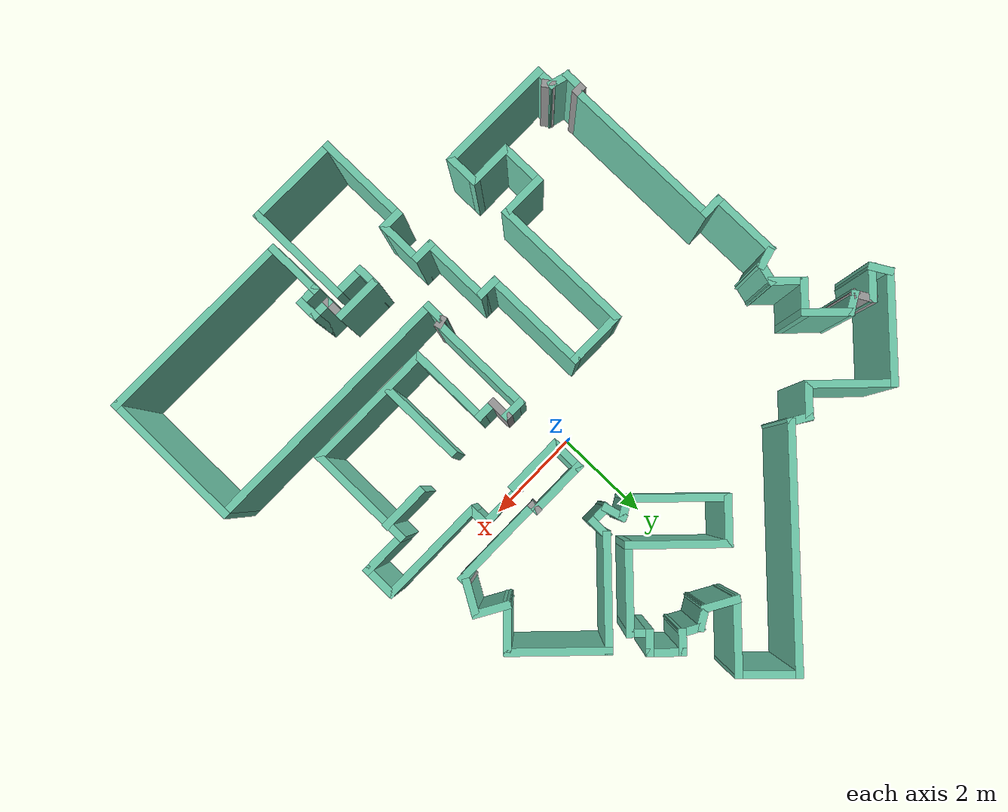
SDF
<?xml version='1.0'?>
<sdf version='1.6'>
  <model name='map_11'>
    <pose frame=''>-0.481268 -0.534059 0 0 -0 0</pose>
    <link name='Wall_0'>
      <collision name='Wall_0_Collision'>
        <geometry>
          <box>
            <size>4.75 0.15 2.5</size>
          </box>
        </geometry>
        <pose frame=''>0 0 1.25 0 -0 0</pose>
      </collision>
      <visual name='Wall_0_Visual'>
        <pose frame=''>0 0 1.25 0 -0 0</pose>
        <geometry>
          <box>
            <size>4.75 0.15 2.5</size>
          </box>
        </geometry>
        <material>
          <script>
            <uri>file://media/materials/scripts/gazebo.material</uri>
            <name>Gazebo/Grey</name>
          </script>
          <ambient>0.435294 0.796078 0.67451 1</ambient>
        </material>
        <meta>
          <layer>0</layer>
        </meta>
      </visual>
      <pose frame=''>-0.933367 4.89876 0 0 -0 -2.35619</pose>
    </link>
    <link name='Wall_1'>
      <collision name='Wall_1_Collision'>
        <geometry>
          <box>
            <size>0.5 0.15 2.5</size>
          </box>
        </geometry>
        <pose frame=''>0 0 1.25 0 -0 0</pose>
      </collision>
      <visual name='Wall_1_Visual'>
        <pose frame=''>0 0 1.25 0 -0 0</pose>
        <geometry>
          <box>
            <size>0.5 0.15 2.5</size>
          </box>
        </geometry>
        <material>
          <script>
            <uri>file://media/materials/scripts/gazebo.material</uri>
            <name>Gazebo/Grey</name>
          </script>
          <ambient>0.435294 0.796078 0.67451 1</ambient>
        </material>
        <meta>
          <layer>0</layer>
        </meta>
      </visual>
      <pose frame=''>-2.71127 3.35991 0 0 -0 2.61799</pose>
    </link>
    <link name='Wall_10'>
      <collision name='Wall_10_Collision'>
        <geometry>
          <box>
            <size>1 0.15 2.5</size>
          </box>
        </geometry>
        <pose frame=''>0 0 1.25 0 -0 0</pose>
      </collision>
      <visual name='Wall_10_Visual'>
        <pose frame=''>0 0 1.25 0 -0 0</pose>
        <geometry>
          <box>
            <size>1 0.15 2.5</size>
          </box>
        </geometry>
        <material>
          <script>
            <uri>file://media/materials/scripts/gazebo.material</uri>
            <name>Gazebo/Grey</name>
          </script>
          <ambient>0.435294 0.796078 0.67451 1</ambient>
        </material>
        <meta>
          <layer>0</layer>
        </meta>
      </visual>
      <pose frame=''>-4.52549 2.36212 0 0 -0 -0.785398</pose>
    </link>
    <link name='Wall_100'>
      <collision name='Wall_100_Collision'>
        <geometry>
          <box>
            <size>1.25445 0.15 2.5</size>
          </box>
        </geometry>
        <pose frame=''>0 0 1.25 0 -0 0</pose>
      </collision>
      <visual name='Wall_100_Visual'>
        <pose frame=''>0 0 1.25 0 -0 0</pose>
        <geometry>
          <box>
            <size>1.25445 0.15 2.5</size>
          </box>
        </geometry>
        <material>
          <script>
            <uri>file://media/materials/scripts/gazebo.material</uri>
            <name>Gazebo/Grey</name>
          </script>
          <ambient>0.435294 0.796078 0.67451 1</ambient>
        </material>
        <meta>
          <layer>0</layer>
        </meta>
      </visual>
      <pose frame=''>1.07905 6.13026 0 0 -0 2.34496</pose>
    </link>
    <link name='Wall_102'>
      <collision name='Wall_102_Collision'>
        <geometry>
          <box>
            <size>1.75 0.15 2.5</size>
          </box>
        </geometry>
        <pose frame=''>0 0 1.25 0 -0 0</pose>
      </collision>
      <visual name='Wall_102_Visual'>
        <pose frame=''>0 0 1.25 0 -0 0</pose>
        <geometry>
          <box>
            <size>1.75 0.15 2.5</size>
          </box>
        </geometry>
        <material>
          <script>
            <uri>file://media/materials/scripts/gazebo.material</uri>
            <name>Gazebo/Grey</name>
          </script>
          <ambient>0.435294 0.796078 0.67451 1</ambient>
        </material>
        <meta>
          <layer>0</layer>
        </meta>
      </visual>
      <pose frame=''>2.21384 -1.64657 0 0 -0 1.5708</pose>
    </link>
    <link name='Wall_104'>
      <collision name='Wall_104_Collision'>
        <geometry>
          <box>
            <size>1 0.15 2.5</size>
          </box>
        </geometry>
        <pose frame=''>0 0 1.25 0 -0 0</pose>
      </collision>
      <visual name='Wall_104_Visual'>
        <pose frame=''>0 0 1.25 0 -0 0</pose>
        <geometry>
          <box>
            <size>1 0.15 2.5</size>
          </box>
        </geometry>
        <material>
          <script>
            <uri>file://media/materials/scripts/gazebo.material</uri>
            <name>Gazebo/Grey</name>
          </script>
          <ambient>0.435294 0.796078 0.67451 1</ambient>
        </material>
        <meta>
          <layer>0</layer>
        </meta>
      </visual>
      <pose frame=''>3.5727 -0.757031 0 0 -0 0</pose>
    </link>
    <link name='Wall_11'>
      <collision name='Wall_11_Collision'>
        <geometry>
          <box>
            <size>0.75 0.15 2.5</size>
          </box>
        </geometry>
        <pose frame=''>0 0 1.25 0 -0 0</pose>
      </collision>
      <visual name='Wall_11_Visual'>
        <pose frame=''>0 0 1.25 0 -0 0</pose>
        <geometry>
          <box>
            <size>0.75 0.15 2.5</size>
          </box>
        </geometry>
        <material>
          <script>
            <uri>file://media/materials/scripts/gazebo.material</uri>
            <name>Gazebo/Grey</name>
          </script>
          <ambient>0.435294 0.796078 0.67451 1</ambient>
        </material>
        <meta>
          <layer>0</layer>
        </meta>
      </visual>
      <pose frame=''>-4.4371 1.84947 0 0 -0 -2.35619</pose>
    </link>
    <link name='Wall_12'>
      <collision name='Wall_12_Collision'>
        <geometry>
          <box>
            <size>0.75 0.15 2.5</size>
          </box>
        </geometry>
        <pose frame=''>0 0 1.25 0 -0 0</pose>
      </collision>
      <visual name='Wall_12_Visual'>
        <pose frame=''>0 0 1.25 0 -0 0</pose>
        <geometry>
          <box>
            <size>0.75 0.15 2.5</size>
          </box>
        </geometry>
        <material>
          <script>
            <uri>file://media/materials/scripts/gazebo.material</uri>
            <name>Gazebo/Grey</name>
          </script>
          <ambient>0.435294 0.796078 0.67451 1</ambient>
        </material>
        <meta>
          <layer>0</layer>
        </meta>
      </visual>
      <pose frame=''>-4.4371 1.42521 0 0 -0 -0.785398</pose>
    </link>
    <link name='Wall_13'>
      <collision name='Wall_13_Collision'>
        <geometry>
          <box>
            <size>0.5 0.15 2.5</size>
          </box>
        </geometry>
        <pose frame=''>0 0 1.25 0 -0 0</pose>
      </collision>
      <visual name='Wall_13_Visual'>
        <pose frame=''>0 0 1.25 0 -0 0</pose>
        <geometry>
          <box>
            <size>0.5 0.15 2.5</size>
          </box>
        </geometry>
        <material>
          <script>
            <uri>file://media/materials/scripts/gazebo.material</uri>
            <name>Gazebo/Grey</name>
          </script>
          <ambient>0.435294 0.796078 0.67451 1</ambient>
        </material>
        <meta>
          <layer>0</layer>
        </meta>
      </visual>
      <pose frame=''>-4.27026 1.04404 0 0 -0 -1.8326</pose>
    </link>
    <link name='Wall_14'>
      <collision name='Wall_14_Collision'>
        <geometry>
          <box>
            <size>0.5 0.15 2.5</size>
          </box>
        </geometry>
        <pose frame=''>0 0 1.25 0 -0 0</pose>
      </collision>
      <visual name='Wall_14_Visual'>
        <pose frame=''>0 0 1.25 0 -0 0</pose>
        <geometry>
          <box>
            <size>0.5 0.15 2.5</size>
          </box>
        </geometry>
        <material>
          <script>
            <uri>file://media/materials/scripts/gazebo.material</uri>
            <name>Gazebo/Grey</name>
          </script>
          <ambient>0.435294 0.796078 0.67451 1</ambient>
        </material>
        <meta>
          <layer>0</layer>
        </meta>
      </visual>
      <pose frame=''>-4.48459 0.829708 0 0 -0 -2.87979</pose>
    </link>
    <link name='Wall_15'>
      <collision name='Wall_15_Collision'>
        <geometry>
          <box>
            <size>1.5 0.15 2.5</size>
          </box>
        </geometry>
        <pose frame=''>0 0 1.25 0 -0 0</pose>
      </collision>
      <visual name='Wall_15_Visual'>
        <pose frame=''>0 0 1.25 0 -0 0</pose>
        <geometry>
          <box>
            <size>1.5 0.15 2.5</size>
          </box>
        </geometry>
        <material>
          <script>
            <uri>file://media/materials/scripts/gazebo.material</uri>
            <name>Gazebo/Grey</name>
          </script>
          <ambient>0.435294 0.796078 0.67451 1</ambient>
        </material>
        <meta>
          <layer>0</layer>
        </meta>
      </visual>
      <pose frame=''>-4.65363 0.109414 0 0 -0 -1.5708</pose>
    </link>
    <link name='Wall_16'>
      <collision name='Wall_16_Collision'>
        <geometry>
          <box>
            <size>0.5 0.15 2.5</size>
          </box>
        </geometry>
        <pose frame=''>0 0 1.25 0 -0 0</pose>
      </collision>
      <visual name='Wall_16_Visual'>
        <pose frame=''>0 0 1.25 0 -0 0</pose>
        <geometry>
          <box>
            <size>0.5 0.15 2.5</size>
          </box>
        </geometry>
        <material>
          <script>
            <uri>file://media/materials/scripts/gazebo.material</uri>
            <name>Gazebo/Grey</name>
          </script>
          <ambient>0.435294 0.796078 0.67451 1</ambient>
        </material>
        <meta>
          <layer>0</layer>
        </meta>
      </visual>
      <pose frame=''>-4.47863 -0.565586 0 0 -0 0</pose>
    </link>
    <link name='Wall_17'>
      <collision name='Wall_17_Collision'>
        <geometry>
          <box>
            <size>3.5 0.15 2.5</size>
          </box>
        </geometry>
        <pose frame=''>0 0 1.25 0 -0 0</pose>
      </collision>
      <visual name='Wall_17_Visual'>
        <pose frame=''>0 0 1.25 0 -0 0</pose>
        <geometry>
          <box>
            <size>3.5 0.15 2.5</size>
          </box>
        </geometry>
        <material>
          <script>
            <uri>file://media/materials/scripts/gazebo.material</uri>
            <name>Gazebo/Grey</name>
          </script>
          <ambient>0.435294 0.796078 0.67451 1</ambient>
        </material>
        <meta>
          <layer>0</layer>
        </meta>
      </visual>
      <pose frame=''>-4.30363 -2.24059 0 0 -0 -1.5708</pose>
    </link>
    <link name='Wall_18'>
      <collision name='Wall_18_Collision'>
        <geometry>
          <box>
            <size>0.25 0.15 2.5</size>
          </box>
        </geometry>
        <pose frame=''>0 0 1.25 0 -0 0</pose>
      </collision>
      <visual name='Wall_18_Visual'>
        <pose frame=''>0 0 1.25 0 -0 0</pose>
        <geometry>
          <box>
            <size>0.25 0.15 2.5</size>
          </box>
        </geometry>
        <material>
          <script>
            <uri>file://media/materials/scripts/gazebo.material</uri>
            <name>Gazebo/Grey</name>
          </script>
          <ambient>1 1 1 1</ambient>
        </material>
        <meta>
          <layer>0</layer>
        </meta>
      </visual>
      <pose frame=''>-4.35363 -3.91559 0 0 -0 3.14159</pose>
    </link>
    <link name='Wall_19'>
      <collision name='Wall_19_Collision'>
        <geometry>
          <box>
            <size>0.5 0.15 2.5</size>
          </box>
        </geometry>
        <pose frame=''>0 0 1.25 0 -0 0</pose>
      </collision>
      <visual name='Wall_19_Visual'>
        <pose frame=''>0 0 1.25 0 -0 0</pose>
        <geometry>
          <box>
            <size>0.5 0.15 2.5</size>
          </box>
        </geometry>
        <material>
          <script>
            <uri>file://media/materials/scripts/gazebo.material</uri>
            <name>Gazebo/Grey</name>
          </script>
          <ambient>0.435294 0.796078 0.67451 1</ambient>
        </material>
        <meta>
          <layer>0</layer>
        </meta>
      </visual>
      <pose frame=''>-4.40363 -4.09059 0 0 -0 -1.5708</pose>
    </link>
    <link name='Wall_2'>
      <collision name='Wall_2_Collision'>
        <geometry>
          <box>
            <size>0.75 0.15 2.5</size>
          </box>
        </geometry>
        <pose frame=''>0 0 1.25 0 -0 0</pose>
      </collision>
      <visual name='Wall_2_Visual'>
        <pose frame=''>0 0 1.25 0 -0 0</pose>
        <geometry>
          <box>
            <size>0.75 0.15 2.5</size>
          </box>
        </geometry>
        <material>
          <script>
            <uri>file://media/materials/scripts/gazebo.material</uri>
            <name>Gazebo/Grey</name>
          </script>
          <ambient>0.435294 0.796078 0.67451 1</ambient>
        </material>
        <meta>
          <layer>0</layer>
        </meta>
      </visual>
      <pose frame=''>-3.07495 3.23528 0 0 -0 -2.35619</pose>
    </link>
    <link name='Wall_20'>
      <collision name='Wall_20_Collision'>
        <geometry>
          <box>
            <size>0.5 0.15 2.5</size>
          </box>
        </geometry>
        <pose frame=''>0 0 1.25 0 -0 0</pose>
      </collision>
      <visual name='Wall_20_Visual'>
        <pose frame=''>0 0 1.25 0 -0 0</pose>
        <geometry>
          <box>
            <size>0.5 0.15 2.5</size>
          </box>
        </geometry>
        <material>
          <script>
            <uri>file://media/materials/scripts/gazebo.material</uri>
            <name>Gazebo/Grey</name>
          </script>
          <ambient>0.435294 0.796078 0.67451 1</ambient>
        </material>
        <meta>
          <layer>0</layer>
        </meta>
      </visual>
      <pose frame=''>-4.23459 -4.31088 0 0 -0 -0.261799</pose>
    </link>
    <link name='Wall_21'>
      <collision name='Wall_21_Collision'>
        <geometry>
          <box>
            <size>0.271718 0.15 2.5</size>
          </box>
        </geometry>
        <pose frame=''>0 0 1.25 0 -0 0</pose>
      </collision>
      <visual name='Wall_21_Visual'>
        <pose frame=''>0 0 1.25 0 -0 0</pose>
        <geometry>
          <box>
            <size>0.271718 0.15 2.5</size>
          </box>
        </geometry>
        <material>
          <script>
            <uri>file://media/materials/scripts/gazebo.material</uri>
            <name>Gazebo/Grey</name>
          </script>
          <ambient>1 1 1 1</ambient>
        </material>
        <meta>
          <layer>0</layer>
        </meta>
      </visual>
      <pose frame=''>-4.03086 -4.40617 0 0 -0 -0.964164</pose>
    </link>
    <link name='Wall_27'>
      <collision name='Wall_27_Collision'>
        <geometry>
          <box>
            <size>0.5 0.15 2.5</size>
          </box>
        </geometry>
        <pose frame=''>0 0 1.25 0 -0 0</pose>
      </collision>
      <visual name='Wall_27_Visual'>
        <pose frame=''>0 0 1.25 0 -0 0</pose>
        <geometry>
          <box>
            <size>0.5 0.15 2.5</size>
          </box>
        </geometry>
        <material>
          <script>
            <uri>file://media/materials/scripts/gazebo.material</uri>
            <name>Gazebo/Grey</name>
          </script>
          <ambient>0.435294 0.796078 0.67451 1</ambient>
        </material>
        <meta>
          <layer>0</layer>
        </meta>
      </visual>
      <pose frame=''>-4.06555 -4.53117 0 0 -0 -1.5708</pose>
    </link>
    <link name='Wall_28'>
      <collision name='Wall_28_Collision'>
        <geometry>
          <box>
            <size>2.5 0.15 2.5</size>
          </box>
        </geometry>
        <pose frame=''>0 0 1.25 0 -0 0</pose>
      </collision>
      <visual name='Wall_28_Visual'>
        <pose frame=''>0 0 1.25 0 -0 0</pose>
        <geometry>
          <box>
            <size>2.5 0.15 2.5</size>
          </box>
        </geometry>
        <material>
          <script>
            <uri>file://media/materials/scripts/gazebo.material</uri>
            <name>Gazebo/Grey</name>
          </script>
          <ambient>0.435294 0.796078 0.67451 1</ambient>
        </material>
        <meta>
          <layer>0</layer>
        </meta>
      </visual>
      <pose frame=''>-2.89055 -4.70617 0 0 -0 0</pose>
    </link>
    <link name='Wall_29'>
      <collision name='Wall_29_Collision'>
        <geometry>
          <box>
            <size>0.75 0.15 2.5</size>
          </box>
        </geometry>
        <pose frame=''>0 0 1.25 0 -0 0</pose>
      </collision>
      <visual name='Wall_29_Visual'>
        <pose frame=''>0 0 1.25 0 -0 0</pose>
        <geometry>
          <box>
            <size>0.75 0.15 2.5</size>
          </box>
        </geometry>
        <material>
          <script>
            <uri>file://media/materials/scripts/gazebo.material</uri>
            <name>Gazebo/Grey</name>
          </script>
          <ambient>0.435294 0.796078 0.67451 1</ambient>
        </material>
        <meta>
          <layer>0</layer>
        </meta>
      </visual>
      <pose frame=''>-1.71555 -4.40617 0 0 -0 1.5708</pose>
    </link>
    <link name='Wall_3'>
      <collision name='Wall_3_Collision'>
        <geometry>
          <box>
            <size>1.75 0.15 2.5</size>
          </box>
        </geometry>
        <pose frame=''>0 0 1.25 0 -0 0</pose>
      </collision>
      <visual name='Wall_3_Visual'>
        <pose frame=''>0 0 1.25 0 -0 0</pose>
        <geometry>
          <box>
            <size>1.75 0.15 2.5</size>
          </box>
        </geometry>
        <material>
          <script>
            <uri>file://media/materials/scripts/gazebo.material</uri>
            <name>Gazebo/Grey</name>
          </script>
          <ambient>0.435294 0.796078 0.67451 1</ambient>
        </material>
        <meta>
          <layer>0</layer>
        </meta>
      </visual>
      <pose frame=''>-3.85277 3.58884 0 0 -0 2.35619</pose>
    </link>
    <link name='Wall_30'>
      <collision name='Wall_30_Collision'>
        <geometry>
          <box>
            <size>1 0.15 2.5</size>
          </box>
        </geometry>
        <pose frame=''>0 0 1.25 0 -0 0</pose>
      </collision>
      <visual name='Wall_30_Visual'>
        <pose frame=''>0 0 1.25 0 -0 0</pose>
        <geometry>
          <box>
            <size>1 0.15 2.5</size>
          </box>
        </geometry>
        <material>
          <script>
            <uri>file://media/materials/scripts/gazebo.material</uri>
            <name>Gazebo/Grey</name>
          </script>
          <ambient>0.435294 0.796078 0.67451 1</ambient>
        </material>
        <meta>
          <layer>0</layer>
        </meta>
      </visual>
      <pose frame=''>-2.14055 -4.10617 0 0 -0 3.14159</pose>
    </link>
    <link name='Wall_31'>
      <collision name='Wall_31_Collision'>
        <geometry>
          <box>
            <size>1 0.15 2.5</size>
          </box>
        </geometry>
        <pose frame=''>0 0 1.25 0 -0 0</pose>
      </collision>
      <visual name='Wall_31_Visual'>
        <pose frame=''>0 0 1.25 0 -0 0</pose>
        <geometry>
          <box>
            <size>1 0.15 2.5</size>
          </box>
        </geometry>
        <material>
          <script>
            <uri>file://media/materials/scripts/gazebo.material</uri>
            <name>Gazebo/Grey</name>
          </script>
          <ambient>0.435294 0.796078 0.67451 1</ambient>
        </material>
        <meta>
          <layer>0</layer>
        </meta>
      </visual>
      <pose frame=''>-2.56555 -3.68117 0 0 -0 1.5708</pose>
    </link>
    <link name='Wall_32'>
      <collision name='Wall_32_Collision'>
        <geometry>
          <box>
            <size>1 0.15 2.5</size>
          </box>
        </geometry>
        <pose frame=''>0 0 1.25 0 -0 0</pose>
      </collision>
      <visual name='Wall_32_Visual'>
        <pose frame=''>0 0 1.25 0 -0 0</pose>
        <geometry>
          <box>
            <size>1 0.15 2.5</size>
          </box>
        </geometry>
        <material>
          <script>
            <uri>file://media/materials/scripts/gazebo.material</uri>
            <name>Gazebo/Grey</name>
          </script>
          <ambient>0.435294 0.796078 0.67451 1</ambient>
        </material>
        <meta>
          <layer>0</layer>
        </meta>
      </visual>
      <pose frame=''>-2.14055 -3.25617 0 0 -0 0</pose>
    </link>
    <link name='Wall_33'>
      <collision name='Wall_33_Collision'>
        <geometry>
          <box>
            <size>3 0.15 2.5</size>
          </box>
        </geometry>
        <pose frame=''>0 0 1.25 0 -0 0</pose>
      </collision>
      <visual name='Wall_33_Visual'>
        <pose frame=''>0 0 1.25 0 -0 0</pose>
        <geometry>
          <box>
            <size>3 0.15 2.5</size>
          </box>
        </geometry>
        <material>
          <script>
            <uri>file://media/materials/scripts/gazebo.material</uri>
            <name>Gazebo/Grey</name>
          </script>
          <ambient>0.435294 0.796078 0.67451 1</ambient>
        </material>
        <meta>
          <layer>0</layer>
        </meta>
      </visual>
      <pose frame=''>-1.71555 -1.83117 0 0 -0 1.5708</pose>
    </link>
    <link name='Wall_34'>
      <collision name='Wall_34_Collision'>
        <geometry>
          <box>
            <size>1.25 0.15 2.5</size>
          </box>
        </geometry>
        <pose frame=''>0 0 1.25 0 -0 0</pose>
      </collision>
      <visual name='Wall_34_Visual'>
        <pose frame=''>0 0 1.25 0 -0 0</pose>
        <geometry>
          <box>
            <size>1.25 0.15 2.5</size>
          </box>
        </geometry>
        <material>
          <script>
            <uri>file://media/materials/scripts/gazebo.material</uri>
            <name>Gazebo/Grey</name>
          </script>
          <ambient>0.435294 0.796078 0.67451 1</ambient>
        </material>
        <meta>
          <layer>0</layer>
        </meta>
      </visual>
      <pose frame=''>-1.16555 -0.406172 0 0 -0 0</pose>
    </link>
    <link name='Wall_35'>
      <collision name='Wall_35_Collision'>
        <geometry>
          <box>
            <size>2.25 0.15 2.5</size>
          </box>
        </geometry>
        <pose frame=''>0 0 1.25 0 -0 0</pose>
      </collision>
      <visual name='Wall_35_Visual'>
        <pose frame=''>0 0 1.25 0 -0 0</pose>
        <geometry>
          <box>
            <size>2.25 0.15 2.5</size>
          </box>
        </geometry>
        <material>
          <script>
            <uri>file://media/materials/scripts/gazebo.material</uri>
            <name>Gazebo/Grey</name>
          </script>
          <ambient>0.435294 0.796078 0.67451 1</ambient>
        </material>
        <meta>
          <layer>0</layer>
        </meta>
      </visual>
      <pose frame=''>-0.615553 -1.45617 0 0 -0 -1.5708</pose>
    </link>
    <link name='Wall_36'>
      <collision name='Wall_36_Collision'>
        <geometry>
          <box>
            <size>0.5 0.15 2.5</size>
          </box>
        </geometry>
        <pose frame=''>0 0 1.25 0 -0 0</pose>
      </collision>
      <visual name='Wall_36_Visual'>
        <pose frame=''>0 0 1.25 0 -0 0</pose>
        <geometry>
          <box>
            <size>0.5 0.15 2.5</size>
          </box>
        </geometry>
        <material>
          <script>
            <uri>file://media/materials/scripts/gazebo.material</uri>
            <name>Gazebo/Grey</name>
          </script>
          <ambient>0.435294 0.796078 0.67451 1</ambient>
        </material>
        <meta>
          <layer>0</layer>
        </meta>
      </visual>
      <pose frame=''>-0.440553 -2.50617 0 0 -0 0</pose>
    </link>
    <link name='Wall_37'>
      <collision name='Wall_37_Collision'>
        <geometry>
          <box>
            <size>1.5 0.15 2.5</size>
          </box>
        </geometry>
        <pose frame=''>0 0 1.25 0 -0 0</pose>
      </collision>
      <visual name='Wall_37_Visual'>
        <pose frame=''>0 0 1.25 0 -0 0</pose>
        <geometry>
          <box>
            <size>1.5 0.15 2.5</size>
          </box>
        </geometry>
        <material>
          <script>
            <uri>file://media/materials/scripts/gazebo.material</uri>
            <name>Gazebo/Grey</name>
          </script>
          <ambient>0.435294 0.796078 0.67451 1</ambient>
        </material>
        <meta>
          <layer>0</layer>
        </meta>
      </visual>
      <pose frame=''>-0.265553 -3.18117 0 0 -0 -1.5708</pose>
    </link>
    <link name='Wall_38'>
      <collision name='Wall_38_Collision'>
        <geometry>
          <box>
            <size>0.5 0.15 2.5</size>
          </box>
        </geometry>
        <pose frame=''>0 0 1.25 0 -0 0</pose>
      </collision>
      <visual name='Wall_38_Visual'>
        <pose frame=''>0 0 1.25 0 -0 0</pose>
        <geometry>
          <box>
            <size>0.5 0.15 2.5</size>
          </box>
        </geometry>
        <material>
          <script>
            <uri>file://media/materials/scripts/gazebo.material</uri>
            <name>Gazebo/Grey</name>
          </script>
          <ambient>0.435294 0.796078 0.67451 1</ambient>
        </material>
        <meta>
          <layer>0</layer>
        </meta>
      </visual>
      <pose frame=''>-0.090554 -3.85617 0 0 -0 0</pose>
    </link>
    <link name='Wall_39'>
      <collision name='Wall_39_Collision'>
        <geometry>
          <box>
            <size>1 0.15 2.5</size>
          </box>
        </geometry>
        <pose frame=''>0 0 1.25 0 -0 0</pose>
      </collision>
      <visual name='Wall_39_Visual'>
        <pose frame=''>0 0 1.25 0 -0 0</pose>
        <geometry>
          <box>
            <size>1 0.15 2.5</size>
          </box>
        </geometry>
        <material>
          <script>
            <uri>file://media/materials/scripts/gazebo.material</uri>
            <name>Gazebo/Grey</name>
          </script>
          <ambient>0.435294 0.796078 0.67451 1</ambient>
        </material>
        <meta>
          <layer>0</layer>
        </meta>
      </visual>
      <pose frame=''>0.084447 -4.28117 0 0 -0 -1.5708</pose>
    </link>
    <link name='Wall_4'>
      <collision name='Wall_4_Collision'>
        <geometry>
          <box>
            <size>2.25 0.15 2.5</size>
          </box>
        </geometry>
        <pose frame=''>0 0 1.25 0 -0 0</pose>
      </collision>
      <visual name='Wall_4_Visual'>
        <pose frame=''>0 0 1.25 0 -0 0</pose>
        <geometry>
          <box>
            <size>2.25 0.15 2.5</size>
          </box>
        </geometry>
        <material>
          <script>
            <uri>file://media/materials/scripts/gazebo.material</uri>
            <name>Gazebo/Grey</name>
          </script>
          <ambient>0.435294 0.796078 0.67451 1</ambient>
        </material>
        <meta>
          <layer>0</layer>
        </meta>
      </visual>
      <pose frame=''>-5.16092 3.41206 0 0 -0 -2.35619</pose>
    </link>
    <link name='Wall_40'>
      <collision name='Wall_40_Collision'>
        <geometry>
          <box>
            <size>0.5 0.15 2.5</size>
          </box>
        </geometry>
        <pose frame=''>0 0 1.25 0 -0 0</pose>
      </collision>
      <visual name='Wall_40_Visual'>
        <pose frame=''>0 0 1.25 0 -0 0</pose>
        <geometry>
          <box>
            <size>0.5 0.15 2.5</size>
          </box>
        </geometry>
        <material>
          <script>
            <uri>file://media/materials/scripts/gazebo.material</uri>
            <name>Gazebo/Grey</name>
          </script>
          <ambient>0.435294 0.796078 0.67451 1</ambient>
        </material>
        <meta>
          <layer>0</layer>
        </meta>
      </visual>
      <pose frame=''>-0.090554 -4.70617 0 0 -0 3.14159</pose>
    </link>
    <link name='Wall_41'>
      <collision name='Wall_41_Collision'>
        <geometry>
          <box>
            <size>2 0.15 2.5</size>
          </box>
        </geometry>
        <pose frame=''>0 0 1.25 0 -0 0</pose>
      </collision>
      <visual name='Wall_41_Visual'>
        <pose frame=''>0 0 1.25 0 -0 0</pose>
        <geometry>
          <box>
            <size>2 0.15 2.5</size>
          </box>
        </geometry>
        <material>
          <script>
            <uri>file://media/materials/scripts/gazebo.material</uri>
            <name>Gazebo/Grey</name>
          </script>
          <ambient>0.435294 0.796078 0.67451 1</ambient>
        </material>
        <meta>
          <layer>0</layer>
        </meta>
      </visual>
      <pose frame=''>-0.265553 -5.63117 0 0 -0 -1.5708</pose>
    </link>
    <link name='Wall_42'>
      <collision name='Wall_42_Collision'>
        <geometry>
          <box>
            <size>2 0.15 2.5</size>
          </box>
        </geometry>
        <pose frame=''>0 0 1.25 0 -0 0</pose>
      </collision>
      <visual name='Wall_42_Visual'>
        <pose frame=''>0 0 1.25 0 -0 0</pose>
        <geometry>
          <box>
            <size>2 0.15 2.5</size>
          </box>
        </geometry>
        <material>
          <script>
            <uri>file://media/materials/scripts/gazebo.material</uri>
            <name>Gazebo/Grey</name>
          </script>
          <ambient>0.435294 0.796078 0.67451 1</ambient>
        </material>
        <meta>
          <layer>0</layer>
        </meta>
      </visual>
      <pose frame=''>0.659447 -6.55617 0 0 -0 0</pose>
    </link>
    <link name='Wall_43'>
      <collision name='Wall_43_Collision'>
        <geometry>
          <box>
            <size>2.25 0.15 2.5</size>
          </box>
        </geometry>
        <pose frame=''>0 0 1.25 0 -0 0</pose>
      </collision>
      <visual name='Wall_43_Visual'>
        <pose frame=''>0 0 1.25 0 -0 0</pose>
        <geometry>
          <box>
            <size>2.25 0.15 2.5</size>
          </box>
        </geometry>
        <material>
          <script>
            <uri>file://media/materials/scripts/gazebo.material</uri>
            <name>Gazebo/Grey</name>
          </script>
          <ambient>0.435294 0.796078 0.67451 1</ambient>
        </material>
        <meta>
          <layer>0</layer>
        </meta>
      </visual>
      <pose frame=''>1.58445 -5.50617 0 0 -0 1.5708</pose>
    </link>
    <link name='Wall_44'>
      <collision name='Wall_44_Collision'>
        <geometry>
          <box>
            <size>0.75 0.15 2.5</size>
          </box>
        </geometry>
        <pose frame=''>0 0 1.25 0 -0 0</pose>
      </collision>
      <visual name='Wall_44_Visual'>
        <pose frame=''>0 0 1.25 0 -0 0</pose>
        <geometry>
          <box>
            <size>0.75 0.15 2.5</size>
          </box>
        </geometry>
        <material>
          <script>
            <uri>file://media/materials/scripts/gazebo.material</uri>
            <name>Gazebo/Grey</name>
          </script>
          <ambient>0.435294 0.796078 0.67451 1</ambient>
        </material>
        <meta>
          <layer>0</layer>
        </meta>
      </visual>
      <pose frame=''>1.28445 -4.45617 0 0 -0 3.14159</pose>
    </link>
    <link name='Wall_45'>
      <collision name='Wall_45_Collision'>
        <geometry>
          <box>
            <size>0.5 0.15 2.5</size>
          </box>
        </geometry>
        <pose frame=''>0 0 1.25 0 -0 0</pose>
      </collision>
      <visual name='Wall_45_Visual'>
        <pose frame=''>0 0 1.25 0 -0 0</pose>
        <geometry>
          <box>
            <size>0.5 0.15 2.5</size>
          </box>
        </geometry>
        <material>
          <script>
            <uri>file://media/materials/scripts/gazebo.material</uri>
            <name>Gazebo/Grey</name>
          </script>
          <ambient>0.435294 0.796078 0.67451 1</ambient>
        </material>
        <meta>
          <layer>0</layer>
        </meta>
      </visual>
      <pose frame=''>0.984447 -4.28117 0 0 -0 1.5708</pose>
    </link>
    <link name='Wall_46'>
      <collision name='Wall_46_Collision'>
        <geometry>
          <box>
            <size>1 0.15 2.5</size>
          </box>
        </geometry>
        <pose frame=''>0 0 1.25 0 -0 0</pose>
      </collision>
      <visual name='Wall_46_Visual'>
        <pose frame=''>0 0 1.25 0 -0 0</pose>
        <geometry>
          <box>
            <size>1 0.15 2.5</size>
          </box>
        </geometry>
        <material>
          <script>
            <uri>file://media/materials/scripts/gazebo.material</uri>
            <name>Gazebo/Grey</name>
          </script>
          <ambient>0.435294 0.796078 0.67451 1</ambient>
        </material>
        <meta>
          <layer>0</layer>
        </meta>
      </visual>
      <pose frame=''>1.40945 -4.10617 0 0 -0 0</pose>
    </link>
    <link name='Wall_47'>
      <collision name='Wall_47_Collision'>
        <geometry>
          <box>
            <size>0.5 0.15 2.5</size>
          </box>
        </geometry>
        <pose frame=''>0 0 1.25 0 -0 0</pose>
      </collision>
      <visual name='Wall_47_Visual'>
        <pose frame=''>0 0 1.25 0 -0 0</pose>
        <geometry>
          <box>
            <size>0.5 0.15 2.5</size>
          </box>
        </geometry>
        <material>
          <script>
            <uri>file://media/materials/scripts/gazebo.material</uri>
            <name>Gazebo/Grey</name>
          </script>
          <ambient>1 1 1 1</ambient>
        </material>
        <meta>
          <layer>0</layer>
        </meta>
      </visual>
      <pose frame=''>1.83445 -4.28117 0 0 -0 -1.5708</pose>
    </link>
    <link name='Wall_48'>
      <collision name='Wall_48_Collision'>
        <geometry>
          <box>
            <size>0.5 0.15 2.5</size>
          </box>
        </geometry>
        <pose frame=''>0 0 1.25 0 -0 0</pose>
      </collision>
      <visual name='Wall_48_Visual'>
        <pose frame=''>0 0 1.25 0 -0 0</pose>
        <geometry>
          <box>
            <size>0.5 0.15 2.5</size>
          </box>
        </geometry>
        <material>
          <script>
            <uri>file://media/materials/scripts/gazebo.material</uri>
            <name>Gazebo/Grey</name>
          </script>
          <ambient>0.435294 0.796078 0.67451 1</ambient>
        </material>
        <meta>
          <layer>0</layer>
        </meta>
      </visual>
      <pose frame=''>2.00945 -4.45617 0 0 -0 0</pose>
    </link>
    <link name='Wall_49'>
      <collision name='Wall_49_Collision'>
        <geometry>
          <box>
            <size>0.5 0.15 2.5</size>
          </box>
        </geometry>
        <pose frame=''>0 0 1.25 0 -0 0</pose>
      </collision>
      <visual name='Wall_49_Visual'>
        <pose frame=''>0 0 1.25 0 -0 0</pose>
        <geometry>
          <box>
            <size>0.5 0.15 2.5</size>
          </box>
        </geometry>
        <material>
          <script>
            <uri>file://media/materials/scripts/gazebo.material</uri>
            <name>Gazebo/Grey</name>
          </script>
          <ambient>0.435294 0.796078 0.67451 1</ambient>
        </material>
        <meta>
          <layer>0</layer>
        </meta>
      </visual>
      <pose frame=''>2.18445 -4.63117 0 0 -0 -1.5708</pose>
    </link>
    <link name='Wall_5'>
      <collision name='Wall_5_Collision'>
        <geometry>
          <box>
            <size>0.5 0.15 2.5</size>
          </box>
        </geometry>
        <pose frame=''>0 0 1.25 0 -0 0</pose>
      </collision>
      <visual name='Wall_5_Visual'>
        <pose frame=''>0 0 1.25 0 -0 0</pose>
        <geometry>
          <box>
            <size>0.5 0.15 2.5</size>
          </box>
        </geometry>
        <material>
          <script>
            <uri>file://media/materials/scripts/gazebo.material</uri>
            <name>Gazebo/Grey</name>
          </script>
          <ambient>0.435294 0.796078 0.67451 1</ambient>
        </material>
        <meta>
          <layer>0</layer>
        </meta>
      </visual>
      <pose frame=''>-5.81588 2.51804 0 0 -0 -1.0472</pose>
    </link>
    <link name='Wall_50'>
      <collision name='Wall_50_Collision'>
        <geometry>
          <box>
            <size>0.5 0.15 2.5</size>
          </box>
        </geometry>
        <pose frame=''>0 0 1.25 0 -0 0</pose>
      </collision>
      <visual name='Wall_50_Visual'>
        <pose frame=''>0 0 1.25 0 -0 0</pose>
        <geometry>
          <box>
            <size>0.5 0.15 2.5</size>
          </box>
        </geometry>
        <material>
          <script>
            <uri>file://media/materials/scripts/gazebo.material</uri>
            <name>Gazebo/Grey</name>
          </script>
          <ambient>0.435294 0.796078 0.67451 1</ambient>
        </material>
        <meta>
          <layer>0</layer>
        </meta>
      </visual>
      <pose frame=''>2.00945 -4.80617 0 0 -0 3.14159</pose>
    </link>
    <link name='Wall_51'>
      <collision name='Wall_51_Collision'>
        <geometry>
          <box>
            <size>1.25 0.15 2.5</size>
          </box>
        </geometry>
        <pose frame=''>0 0 1.25 0 -0 0</pose>
      </collision>
      <visual name='Wall_51_Visual'>
        <pose frame=''>0 0 1.25 0 -0 0</pose>
        <geometry>
          <box>
            <size>1.25 0.15 2.5</size>
          </box>
        </geometry>
        <material>
          <script>
            <uri>file://media/materials/scripts/gazebo.material</uri>
            <name>Gazebo/Grey</name>
          </script>
          <ambient>0.435294 0.796078 0.67451 1</ambient>
        </material>
        <meta>
          <layer>0</layer>
        </meta>
      </visual>
      <pose frame=''>1.83445 -5.35617 0 0 -0 -1.5708</pose>
    </link>
    <link name='Wall_52'>
      <collision name='Wall_52_Collision'>
        <geometry>
          <box>
            <size>4.25 0.15 2.5</size>
          </box>
        </geometry>
        <pose frame=''>0 0 1.25 0 -0 0</pose>
      </collision>
      <visual name='Wall_52_Visual'>
        <pose frame=''>0 0 1.25 0 -0 0</pose>
        <geometry>
          <box>
            <size>4.25 0.15 2.5</size>
          </box>
        </geometry>
        <material>
          <script>
            <uri>file://media/materials/scripts/gazebo.material</uri>
            <name>Gazebo/Grey</name>
          </script>
          <ambient>0.435294 0.796078 0.67451 1</ambient>
        </material>
        <meta>
          <layer>0</layer>
        </meta>
      </visual>
      <pose frame=''>3.88445 -5.90617 0 0 -0 0</pose>
    </link>
    <link name='Wall_53'>
      <collision name='Wall_53_Collision'>
        <geometry>
          <box>
            <size>3 0.15 2.5</size>
          </box>
        </geometry>
        <pose frame=''>0 0 1.25 0 -0 0</pose>
      </collision>
      <visual name='Wall_53_Visual'>
        <pose frame=''>0 0 1.25 0 -0 0</pose>
        <geometry>
          <box>
            <size>3 0.15 2.5</size>
          </box>
        </geometry>
        <material>
          <script>
            <uri>file://media/materials/scripts/gazebo.material</uri>
            <name>Gazebo/Grey</name>
          </script>
          <ambient>0.435294 0.796078 0.67451 1</ambient>
        </material>
        <meta>
          <layer>0</layer>
        </meta>
      </visual>
      <pose frame=''>5.93445 -4.48117 0 0 -0 1.5708</pose>
    </link>
    <link name='Wall_54'>
      <collision name='Wall_54_Collision'>
        <geometry>
          <box>
            <size>5.5 0.15 2.5</size>
          </box>
        </geometry>
        <pose frame=''>0 0 1.25 0 -0 0</pose>
      </collision>
      <visual name='Wall_54_Visual'>
        <pose frame=''>0 0 1.25 0 -0 0</pose>
        <geometry>
          <box>
            <size>5.5 0.15 2.5</size>
          </box>
        </geometry>
        <material>
          <script>
            <uri>file://media/materials/scripts/gazebo.material</uri>
            <name>Gazebo/Grey</name>
          </script>
          <ambient>0.435294 0.796078 0.67451 1</ambient>
        </material>
        <meta>
          <layer>0</layer>
        </meta>
      </visual>
      <pose frame=''>3.25945 -3.05617 0 0 -0 3.14159</pose>
    </link>
    <link name='Wall_55'>
      <collision name='Wall_55_Collision'>
        <geometry>
          <box>
            <size>0.5 0.15 2.5</size>
          </box>
        </geometry>
        <pose frame=''>0 0 1.25 0 -0 0</pose>
      </collision>
      <visual name='Wall_55_Visual'>
        <pose frame=''>0 0 1.25 0 -0 0</pose>
        <geometry>
          <box>
            <size>0.5 0.15 2.5</size>
          </box>
        </geometry>
        <material>
          <script>
            <uri>file://media/materials/scripts/gazebo.material</uri>
            <name>Gazebo/Grey</name>
          </script>
          <ambient>0.435294 0.796078 0.67451 1</ambient>
        </material>
        <meta>
          <layer>0</layer>
        </meta>
      </visual>
      <pose frame=''>0.584447 -2.88117 0 0 -0 1.5708</pose>
    </link>
    <link name='Wall_56'>
      <collision name='Wall_56_Collision'>
        <geometry>
          <box>
            <size>0.25 0.15 2.5</size>
          </box>
        </geometry>
        <pose frame=''>0 0 1.25 0 -0 0</pose>
      </collision>
      <visual name='Wall_56_Visual'>
        <pose frame=''>0 0 1.25 0 -0 0</pose>
        <geometry>
          <box>
            <size>0.25 0.15 2.5</size>
          </box>
        </geometry>
        <material>
          <script>
            <uri>file://media/materials/scripts/gazebo.material</uri>
            <name>Gazebo/Grey</name>
          </script>
          <ambient>1 1 1 1</ambient>
        </material>
        <meta>
          <layer>0</layer>
        </meta>
      </visual>
      <pose frame=''>0.632743 -2.69323 0 0 -0 0.261799</pose>
    </link>
    <link name='Wall_57'>
      <collision name='Wall_57_Collision'>
        <geometry>
          <box>
            <size>2.25 0.15 2.5</size>
          </box>
        </geometry>
        <pose frame=''>0 0 1.25 0 -0 0</pose>
      </collision>
      <visual name='Wall_57_Visual'>
        <pose frame=''>0 0 1.25 0 -0 0</pose>
        <geometry>
          <box>
            <size>2.25 0.15 2.5</size>
          </box>
        </geometry>
        <material>
          <script>
            <uri>file://media/materials/scripts/gazebo.material</uri>
            <name>Gazebo/Grey</name>
          </script>
          <ambient>0.435294 0.796078 0.67451 1</ambient>
        </material>
        <meta>
          <layer>0</layer>
        </meta>
      </visual>
      <pose frame=''>0.681039 -1.63029 0 0 -0 1.5708</pose>
    </link>
    <link name='Wall_58'>
      <collision name='Wall_58_Collision'>
        <geometry>
          <box>
            <size>0.5 0.15 2.5</size>
          </box>
        </geometry>
        <pose frame=''>0 0 1.25 0 -0 0</pose>
      </collision>
      <visual name='Wall_58_Visual'>
        <pose frame=''>0 0 1.25 0 -0 0</pose>
        <geometry>
          <box>
            <size>0.5 0.15 2.5</size>
          </box>
        </geometry>
        <material>
          <script>
            <uri>file://media/materials/scripts/gazebo.material</uri>
            <name>Gazebo/Grey</name>
          </script>
          <ambient>0.435294 0.796078 0.67451 1</ambient>
        </material>
        <meta>
          <layer>0</layer>
        </meta>
      </visual>
      <pose frame=''>0.856039 -0.580291 0 0 -0 0</pose>
    </link>
    <link name='Wall_59'>
      <collision name='Wall_59_Collision'>
        <geometry>
          <box>
            <size>0.5 0.15 2.5</size>
          </box>
        </geometry>
        <pose frame=''>0 0 1.25 0 -0 0</pose>
      </collision>
      <visual name='Wall_59_Visual'>
        <pose frame=''>0 0 1.25 0 -0 0</pose>
        <geometry>
          <box>
            <size>0.5 0.15 2.5</size>
          </box>
        </geometry>
        <material>
          <script>
            <uri>file://media/materials/scripts/gazebo.material</uri>
            <name>Gazebo/Grey</name>
          </script>
          <ambient>1 1 1 1</ambient>
        </material>
        <meta>
          <layer>0</layer>
        </meta>
      </visual>
      <pose frame=''>1.03104 -0.755291 0 0 -0 -1.5708</pose>
    </link>
    <link name='Wall_6'>
      <collision name='Wall_6_Collision'>
        <geometry>
          <box>
            <size>0.75 0.15 2.5</size>
          </box>
        </geometry>
        <pose frame=''>0 0 1.25 0 -0 0</pose>
      </collision>
      <visual name='Wall_6_Visual'>
        <pose frame=''>0 0 1.25 0 -0 0</pose>
        <geometry>
          <box>
            <size>0.75 0.15 2.5</size>
          </box>
        </geometry>
        <material>
          <script>
            <uri>file://media/materials/scripts/gazebo.material</uri>
            <name>Gazebo/Grey</name>
          </script>
          <ambient>0.435294 0.796078 0.67451 1</ambient>
        </material>
        <meta>
          <layer>0</layer>
        </meta>
      </visual>
      <pose frame=''>-5.51625 2.57862 0 0 -0 0.785398</pose>
    </link>
    <link name='Wall_60'>
      <collision name='Wall_60_Collision'>
        <geometry>
          <box>
            <size>0.5 0.15 2.5</size>
          </box>
        </geometry>
        <pose frame=''>0 0 1.25 0 -0 0</pose>
      </collision>
      <visual name='Wall_60_Visual'>
        <pose frame=''>0 0 1.25 0 -0 0</pose>
        <geometry>
          <box>
            <size>0.5 0.15 2.5</size>
          </box>
        </geometry>
        <material>
          <script>
            <uri>file://media/materials/scripts/gazebo.material</uri>
            <name>Gazebo/Grey</name>
          </script>
          <ambient>0.435294 0.796078 0.67451 1</ambient>
        </material>
        <meta>
          <layer>0</layer>
        </meta>
      </visual>
      <pose frame=''>1.20604 -0.930291 0 0 -0 0</pose>
    </link>
    <link name='Wall_61'>
      <collision name='Wall_61_Collision'>
        <geometry>
          <box>
            <size>1.75 0.15 2.5</size>
          </box>
        </geometry>
        <pose frame=''>0 0 1.25 0 -0 0</pose>
      </collision>
      <visual name='Wall_61_Visual'>
        <pose frame=''>0 0 1.25 0 -0 0</pose>
        <geometry>
          <box>
            <size>1.75 0.15 2.5</size>
          </box>
        </geometry>
        <material>
          <script>
            <uri>file://media/materials/scripts/gazebo.material</uri>
            <name>Gazebo/Grey</name>
          </script>
          <ambient>0.435294 0.796078 0.67451 1</ambient>
        </material>
        <meta>
          <layer>0</layer>
        </meta>
      </visual>
      <pose frame=''>1.38104 -1.73029 0 0 -0 -1.5708</pose>
    </link>
    <link name='Wall_62'>
      <collision name='Wall_62_Collision'>
        <geometry>
          <box>
            <size>2.75 0.15 2.5</size>
          </box>
        </geometry>
        <pose frame=''>0 0 1.25 0 -0 0</pose>
      </collision>
      <visual name='Wall_62_Visual'>
        <pose frame=''>0 0 1.25 0 -0 0</pose>
        <geometry>
          <box>
            <size>2.75 0.15 2.5</size>
          </box>
        </geometry>
        <material>
          <script>
            <uri>file://media/materials/scripts/gazebo.material</uri>
            <name>Gazebo/Grey</name>
          </script>
          <ambient>0.435294 0.796078 0.67451 1</ambient>
        </material>
        <meta>
          <layer>0</layer>
        </meta>
      </visual>
      <pose frame=''>2.68104 -2.53029 0 0 -0 0</pose>
    </link>
    <link name='Wall_63'>
      <collision name='Wall_63_Collision'>
        <geometry>
          <box>
            <size>2.25 0.15 2.5</size>
          </box>
        </geometry>
        <pose frame=''>0 0 1.25 0 -0 0</pose>
      </collision>
      <visual name='Wall_63_Visual'>
        <pose frame=''>0 0 1.25 0 -0 0</pose>
        <geometry>
          <box>
            <size>2.25 0.15 2.5</size>
          </box>
        </geometry>
        <material>
          <script>
            <uri>file://media/materials/scripts/gazebo.material</uri>
            <name>Gazebo/Grey</name>
          </script>
          <ambient>0.435294 0.796078 0.67451 1</ambient>
        </material>
        <meta>
          <layer>0</layer>
        </meta>
      </visual>
      <pose frame=''>3.98104 -1.48029 0 0 -0 1.5708</pose>
    </link>
    <link name='Wall_64'>
      <collision name='Wall_64_Collision'>
        <geometry>
          <box>
            <size>1 0.15 2.5</size>
          </box>
        </geometry>
        <pose frame=''>0 0 1.25 0 -0 0</pose>
      </collision>
      <visual name='Wall_64_Visual'>
        <pose frame=''>0 0 1.25 0 -0 0</pose>
        <geometry>
          <box>
            <size>1 0.15 2.5</size>
          </box>
        </geometry>
        <material>
          <script>
            <uri>file://media/materials/scripts/gazebo.material</uri>
            <name>Gazebo/Grey</name>
          </script>
          <ambient>0.435294 0.796078 0.67451 1</ambient>
        </material>
        <meta>
          <layer>0</layer>
        </meta>
      </visual>
      <pose frame=''>4.40604 -0.430291 0 0 -0 0</pose>
    </link>
    <link name='Wall_65'>
      <collision name='Wall_65_Collision'>
        <geometry>
          <box>
            <size>0.75 0.15 2.5</size>
          </box>
        </geometry>
        <pose frame=''>0 0 1.25 0 -0 0</pose>
      </collision>
      <visual name='Wall_65_Visual'>
        <pose frame=''>0 0 1.25 0 -0 0</pose>
        <geometry>
          <box>
            <size>0.75 0.15 2.5</size>
          </box>
        </geometry>
        <material>
          <script>
            <uri>file://media/materials/scripts/gazebo.material</uri>
            <name>Gazebo/Grey</name>
          </script>
          <ambient>0.435294 0.796078 0.67451 1</ambient>
        </material>
        <meta>
          <layer>0</layer>
        </meta>
      </visual>
      <pose frame=''>4.83104 -0.130291 0 0 -0 1.5708</pose>
    </link>
    <link name='Wall_66'>
      <collision name='Wall_66_Collision'>
        <geometry>
          <box>
            <size>2.25 0.15 2.5</size>
          </box>
        </geometry>
        <pose frame=''>0 0 1.25 0 -0 0</pose>
      </collision>
      <visual name='Wall_66_Visual'>
        <pose frame=''>0 0 1.25 0 -0 0</pose>
        <geometry>
          <box>
            <size>2.25 0.15 2.5</size>
          </box>
        </geometry>
        <material>
          <script>
            <uri>file://media/materials/scripts/gazebo.material</uri>
            <name>Gazebo/Grey</name>
          </script>
          <ambient>0.435294 0.796078 0.67451 1</ambient>
        </material>
        <meta>
          <layer>0</layer>
        </meta>
      </visual>
      <pose frame=''>3.78104 0.169709 0 0 -0 3.14159</pose>
    </link>
    <link name='Wall_67'>
      <collision name='Wall_67_Collision'>
        <geometry>
          <box>
            <size>0.5 0.15 2.5</size>
          </box>
        </geometry>
        <pose frame=''>0 0 1.25 0 -0 0</pose>
      </collision>
      <visual name='Wall_67_Visual'>
        <pose frame=''>0 0 1.25 0 -0 0</pose>
        <geometry>
          <box>
            <size>0.5 0.15 2.5</size>
          </box>
        </geometry>
        <material>
          <script>
            <uri>file://media/materials/scripts/gazebo.material</uri>
            <name>Gazebo/Grey</name>
          </script>
          <ambient>0.435294 0.796078 0.67451 1</ambient>
        </material>
        <meta>
          <layer>0</layer>
        </meta>
      </visual>
      <pose frame=''>2.73104 0.344709 0 0 -0 1.5708</pose>
    </link>
    <link name='Wall_68'>
      <collision name='Wall_68_Collision'>
        <geometry>
          <box>
            <size>1 0.15 2.5</size>
          </box>
        </geometry>
        <pose frame=''>0 0 1.25 0 -0 0</pose>
      </collision>
      <visual name='Wall_68_Visual'>
        <pose frame=''>0 0 1.25 0 -0 0</pose>
        <geometry>
          <box>
            <size>1 0.15 2.5</size>
          </box>
        </geometry>
        <material>
          <script>
            <uri>file://media/materials/scripts/gazebo.material</uri>
            <name>Gazebo/Grey</name>
          </script>
          <ambient>0.435294 0.796078 0.67451 1</ambient>
        </material>
        <meta>
          <layer>0</layer>
        </meta>
      </visual>
      <pose frame=''>2.30604 0.519709 0 0 -0 3.14159</pose>
    </link>
    <link name='Wall_69'>
      <collision name='Wall_69_Collision'>
        <geometry>
          <box>
            <size>0.25 0.15 2.5</size>
          </box>
        </geometry>
        <pose frame=''>0 0 1.25 0 -0 0</pose>
      </collision>
      <visual name='Wall_69_Visual'>
        <pose frame=''>0 0 1.25 0 -0 0</pose>
        <geometry>
          <box>
            <size>0.25 0.15 2.5</size>
          </box>
        </geometry>
        <material>
          <script>
            <uri>file://media/materials/scripts/gazebo.material</uri>
            <name>Gazebo/Grey</name>
          </script>
          <ambient>1 1 1 1</ambient>
        </material>
        <meta>
          <layer>0</layer>
        </meta>
      </visual>
      <pose frame=''>1.88104 0.469709 0 0 -0 -1.5708</pose>
    </link>
    <link name='Wall_7'>
      <collision name='Wall_7_Collision'>
        <geometry>
          <box>
            <size>0.5 0.15 2.5</size>
          </box>
        </geometry>
        <pose frame=''>0 0 1.25 0 -0 0</pose>
      </collision>
      <visual name='Wall_7_Visual'>
        <pose frame=''>0 0 1.25 0 -0 0</pose>
        <geometry>
          <box>
            <size>0.5 0.15 2.5</size>
          </box>
        </geometry>
        <material>
          <script>
            <uri>file://media/materials/scripts/gazebo.material</uri>
            <name>Gazebo/Grey</name>
          </script>
          <ambient>1 1 1 1</ambient>
        </material>
        <meta>
          <layer>0</layer>
        </meta>
      </visual>
      <pose frame=''>-5.21662 2.6392 0 0 -0 -1.0472</pose>
    </link>
    <link name='Wall_70'>
      <collision name='Wall_70_Collision'>
        <geometry>
          <box>
            <size>1.25 0.15 2.5</size>
          </box>
        </geometry>
        <pose frame=''>0 0 1.25 0 -0 0</pose>
      </collision>
      <visual name='Wall_70_Visual'>
        <pose frame=''>0 0 1.25 0 -0 0</pose>
        <geometry>
          <box>
            <size>1.25 0.15 2.5</size>
          </box>
        </geometry>
        <material>
          <script>
            <uri>file://media/materials/scripts/gazebo.material</uri>
            <name>Gazebo/Grey</name>
          </script>
          <ambient>0.435294 0.796078 0.67451 1</ambient>
        </material>
        <meta>
          <layer>0</layer>
        </meta>
      </visual>
      <pose frame=''>1.33104 0.419709 0 0 -0 3.14159</pose>
    </link>
    <link name='Wall_71'>
      <collision name='Wall_71_Collision'>
        <geometry>
          <box>
            <size>0.75 0.15 2.5</size>
          </box>
        </geometry>
        <pose frame=''>0 0 1.25 0 -0 0</pose>
      </collision>
      <visual name='Wall_71_Visual'>
        <pose frame=''>0 0 1.25 0 -0 0</pose>
        <geometry>
          <box>
            <size>0.75 0.15 2.5</size>
          </box>
        </geometry>
        <material>
          <script>
            <uri>file://media/materials/scripts/gazebo.material</uri>
            <name>Gazebo/Grey</name>
          </script>
          <ambient>0.435294 0.796078 0.67451 1</ambient>
        </material>
        <meta>
          <layer>0</layer>
        </meta>
      </visual>
      <pose frame=''>0.781039 0.719709 0 0 -0 1.5708</pose>
    </link>
    <link name='Wall_72'>
      <collision name='Wall_72_Collision'>
        <geometry>
          <box>
            <size>1.25 0.15 2.5</size>
          </box>
        </geometry>
        <pose frame=''>0 0 1.25 0 -0 0</pose>
      </collision>
      <visual name='Wall_72_Visual'>
        <pose frame=''>0 0 1.25 0 -0 0</pose>
        <geometry>
          <box>
            <size>1.25 0.15 2.5</size>
          </box>
        </geometry>
        <material>
          <script>
            <uri>file://media/materials/scripts/gazebo.material</uri>
            <name>Gazebo/Grey</name>
          </script>
          <ambient>0.435294 0.796078 0.67451 1</ambient>
        </material>
        <meta>
          <layer>0</layer>
        </meta>
      </visual>
      <pose frame=''>1.33104 1.01971 0 0 -0 0</pose>
    </link>
    <link name='Wall_75'>
      <collision name='Wall_75_Collision'>
        <geometry>
          <box>
            <size>0.25 0.15 2.5</size>
          </box>
        </geometry>
        <pose frame=''>0 0 1.25 0 -0 0</pose>
      </collision>
      <visual name='Wall_75_Visual'>
        <pose frame=''>0 0 1.25 0 -0 0</pose>
        <geometry>
          <box>
            <size>0.25 0.15 2.5</size>
          </box>
        </geometry>
        <material>
          <script>
            <uri>file://media/materials/scripts/gazebo.material</uri>
            <name>Gazebo/Grey</name>
          </script>
          <ambient>1 1 1 1</ambient>
        </material>
        <meta>
          <layer>0</layer>
        </meta>
      </visual>
      <pose frame=''>1.88104 0.969709 0 0 -0 -1.5708</pose>
    </link>
    <link name='Wall_76'>
      <collision name='Wall_76_Collision'>
        <geometry>
          <box>
            <size>2 0.15 2.5</size>
          </box>
        </geometry>
        <pose frame=''>0 0 1.25 0 -0 0</pose>
      </collision>
      <visual name='Wall_76_Visual'>
        <pose frame=''>0 0 1.25 0 -0 0</pose>
        <geometry>
          <box>
            <size>2 0.15 2.5</size>
          </box>
        </geometry>
        <material>
          <script>
            <uri>file://media/materials/scripts/gazebo.material</uri>
            <name>Gazebo/Grey</name>
          </script>
          <ambient>0.435294 0.796078 0.67451 1</ambient>
        </material>
        <meta>
          <layer>0</layer>
        </meta>
      </visual>
      <pose frame=''>2.80604 0.919709 0 0 -0 0</pose>
    </link>
    <link name='Wall_77'>
      <collision name='Wall_77_Collision'>
        <geometry>
          <box>
            <size>0.25 0.15 2.5</size>
          </box>
        </geometry>
        <pose frame=''>0 0 1.25 0 -0 0</pose>
      </collision>
      <visual name='Wall_77_Visual'>
        <pose frame=''>0 0 1.25 0 -0 0</pose>
        <geometry>
          <box>
            <size>0.25 0.15 2.5</size>
          </box>
        </geometry>
        <material>
          <script>
            <uri>file://media/materials/scripts/gazebo.material</uri>
            <name>Gazebo/Grey</name>
          </script>
          <ambient>1 1 1 1</ambient>
        </material>
        <meta>
          <layer>0</layer>
        </meta>
      </visual>
      <pose frame=''>3.73104 0.969709 0 0 -0 1.5708</pose>
    </link>
    <link name='Wall_78'>
      <collision name='Wall_78_Collision'>
        <geometry>
          <box>
            <size>0.75 0.15 2.5</size>
          </box>
        </geometry>
        <pose frame=''>0 0 1.25 0 -0 0</pose>
      </collision>
      <visual name='Wall_78_Visual'>
        <pose frame=''>0 0 1.25 0 -0 0</pose>
        <geometry>
          <box>
            <size>0.75 0.15 2.5</size>
          </box>
        </geometry>
        <material>
          <script>
            <uri>file://media/materials/scripts/gazebo.material</uri>
            <name>Gazebo/Grey</name>
          </script>
          <ambient>0.435294 0.796078 0.67451 1</ambient>
        </material>
        <meta>
          <layer>0</layer>
        </meta>
      </visual>
      <pose frame=''>3.88104 1.27952 0 0 -0 1.0472</pose>
    </link>
    <link name='Wall_79'>
      <collision name='Wall_79_Collision'>
        <geometry>
          <box>
            <size>0.75 0.15 2.5</size>
          </box>
        </geometry>
        <pose frame=''>0 0 1.25 0 -0 0</pose>
      </collision>
      <visual name='Wall_79_Visual'>
        <pose frame=''>0 0 1.25 0 -0 0</pose>
        <geometry>
          <box>
            <size>0.75 0.15 2.5</size>
          </box>
        </geometry>
        <material>
          <script>
            <uri>file://media/materials/scripts/gazebo.material</uri>
            <name>Gazebo/Grey</name>
          </script>
          <ambient>0.435294 0.796078 0.67451 1</ambient>
        </material>
        <meta>
          <layer>0</layer>
        </meta>
      </visual>
      <pose frame=''>3.77123 1.68932 0 0 -0 2.61799</pose>
    </link>
    <link name='Wall_8'>
      <collision name='Wall_8_Collision'>
        <geometry>
          <box>
            <size>0.15 0.15 2.5</size>
          </box>
        </geometry>
        <pose frame=''>0 0 1.25 0 -0 0</pose>
      </collision>
      <visual name='Wall_8_Visual'>
        <pose frame=''>0 0 1.25 0 -0 0</pose>
        <geometry>
          <box>
            <size>0.15 0.15 2.5</size>
          </box>
        </geometry>
        <material>
          <script>
            <uri>file://media/materials/scripts/gazebo.material</uri>
            <name>Gazebo/Grey</name>
          </script>
          <ambient>1 1 1 1</ambient>
        </material>
        <meta>
          <layer>0</layer>
        </meta>
      </visual>
      <pose frame=''>-5.12912 2.48764 0 0 -0 0</pose>
    </link>
    <link name='Wall_80'>
      <collision name='Wall_80_Collision'>
        <geometry>
          <box>
            <size>1 0.15 2.5</size>
          </box>
        </geometry>
        <pose frame=''>0 0 1.25 0 -0 0</pose>
      </collision>
      <visual name='Wall_80_Visual'>
        <pose frame=''>0 0 1.25 0 -0 0</pose>
        <geometry>
          <box>
            <size>1 0.15 2.5</size>
          </box>
        </geometry>
        <material>
          <script>
            <uri>file://media/materials/scripts/gazebo.material</uri>
            <name>Gazebo/Grey</name>
          </script>
          <ambient>0.435294 0.796078 0.67451 1</ambient>
        </material>
        <meta>
          <layer>0</layer>
        </meta>
      </visual>
      <pose frame=''>3.81194 2.13985 0 0 -0 0.785398</pose>
    </link>
    <link name='Wall_82'>
      <collision name='Wall_82_Collision'>
        <geometry>
          <box>
            <size>2 0.15 2.5</size>
          </box>
        </geometry>
        <pose frame=''>0 0 1.25 0 -0 0</pose>
      </collision>
      <visual name='Wall_82_Visual'>
        <pose frame=''>0 0 1.25 0 -0 0</pose>
        <geometry>
          <box>
            <size>2 0.15 2.5</size>
          </box>
        </geometry>
        <material>
          <script>
            <uri>file://media/materials/scripts/gazebo.material</uri>
            <name>Gazebo/Grey</name>
          </script>
          <ambient>0.435294 0.796078 0.67451 1</ambient>
        </material>
        <meta>
          <layer>0</layer>
        </meta>
      </visual>
      <pose frame=''>3.45839 3.09444 0 0 -0 2.35619</pose>
    </link>
    <link name='Wall_83'>
      <collision name='Wall_83_Collision'>
        <geometry>
          <box>
            <size>2.25 0.15 2.5</size>
          </box>
        </geometry>
        <pose frame=''>0 0 1.25 0 -0 0</pose>
      </collision>
      <visual name='Wall_83_Visual'>
        <pose frame=''>0 0 1.25 0 -0 0</pose>
        <geometry>
          <box>
            <size>2.25 0.15 2.5</size>
          </box>
        </geometry>
        <material>
          <script>
            <uri>file://media/materials/scripts/gazebo.material</uri>
            <name>Gazebo/Grey</name>
          </script>
          <ambient>0.435294 0.796078 0.67451 1</ambient>
        </material>
        <meta>
          <layer>0</layer>
        </meta>
      </visual>
      <pose frame=''>2.06185 3.00605 0 0 -0 -2.35619</pose>
    </link>
    <link name='Wall_84'>
      <collision name='Wall_84_Collision'>
        <geometry>
          <box>
            <size>0.5 0.15 2.5</size>
          </box>
        </geometry>
        <pose frame=''>0 0 1.25 0 -0 0</pose>
      </collision>
      <visual name='Wall_84_Visual'>
        <pose frame=''>0 0 1.25 0 -0 0</pose>
        <geometry>
          <box>
            <size>0.5 0.15 2.5</size>
          </box>
        </geometry>
        <material>
          <script>
            <uri>file://media/materials/scripts/gazebo.material</uri>
            <name>Gazebo/Grey</name>
          </script>
          <ambient>0.435294 0.796078 0.67451 1</ambient>
        </material>
        <meta>
          <layer>0</layer>
        </meta>
      </visual>
      <pose frame=''>1.31939 2.08859 0 0 -0 -1.5708</pose>
    </link>
    <link name='Wall_85'>
      <collision name='Wall_85_Collision'>
        <geometry>
          <box>
            <size>0.5 0.15 2.5</size>
          </box>
        </geometry>
        <pose frame=''>0 0 1.25 0 -0 0</pose>
      </collision>
      <visual name='Wall_85_Visual'>
        <pose frame=''>0 0 1.25 0 -0 0</pose>
        <geometry>
          <box>
            <size>0.5 0.15 2.5</size>
          </box>
        </geometry>
        <material>
          <script>
            <uri>file://media/materials/scripts/gazebo.material</uri>
            <name>Gazebo/Grey</name>
          </script>
          <ambient>0.435294 0.796078 0.67451 1</ambient>
        </material>
        <meta>
          <layer>0</layer>
        </meta>
      </visual>
      <pose frame=''>1.14439 1.91359 0 0 -0 3.14159</pose>
    </link>
    <link name='Wall_86'>
      <collision name='Wall_86_Collision'>
        <geometry>
          <box>
            <size>0.5 0.15 2.5</size>
          </box>
        </geometry>
        <pose frame=''>0 0 1.25 0 -0 0</pose>
      </collision>
      <visual name='Wall_86_Visual'>
        <pose frame=''>0 0 1.25 0 -0 0</pose>
        <geometry>
          <box>
            <size>0.5 0.15 2.5</size>
          </box>
        </geometry>
        <material>
          <script>
            <uri>file://media/materials/scripts/gazebo.material</uri>
            <name>Gazebo/Grey</name>
          </script>
          <ambient>0.435294 0.796078 0.67451 1</ambient>
        </material>
        <meta>
          <layer>0</layer>
        </meta>
      </visual>
      <pose frame=''>0.9241 2.08263 0 0 -0 1.8326</pose>
    </link>
    <link name='Wall_87'>
      <collision name='Wall_87_Collision'>
        <geometry>
          <box>
            <size>0.5 0.15 2.5</size>
          </box>
        </geometry>
        <pose frame=''>0 0 1.25 0 -0 0</pose>
      </collision>
      <visual name='Wall_87_Visual'>
        <pose frame=''>0 0 1.25 0 -0 0</pose>
        <geometry>
          <box>
            <size>0.5 0.15 2.5</size>
          </box>
        </geometry>
        <material>
          <script>
            <uri>file://media/materials/scripts/gazebo.material</uri>
            <name>Gazebo/Grey</name>
          </script>
          <ambient>0.435294 0.796078 0.67451 1</ambient>
        </material>
        <meta>
          <layer>0</layer>
        </meta>
      </visual>
      <pose frame=''>0.727252 2.16416 0 0 -0 -2.61799</pose>
    </link>
    <link name='Wall_88'>
      <collision name='Wall_88_Collision'>
        <geometry>
          <box>
            <size>2 0.15 2.5</size>
          </box>
        </geometry>
        <pose frame=''>0 0 1.25 0 -0 0</pose>
      </collision>
      <visual name='Wall_88_Visual'>
        <pose frame=''>0 0 1.25 0 -0 0</pose>
        <geometry>
          <box>
            <size>2 0.15 2.5</size>
          </box>
        </geometry>
        <material>
          <script>
            <uri>file://media/materials/scripts/gazebo.material</uri>
            <name>Gazebo/Grey</name>
          </script>
          <ambient>0.435294 0.796078 0.67451 1</ambient>
        </material>
        <meta>
          <layer>0</layer>
        </meta>
      </visual>
      <pose frame=''>-0.078377 2.73074 0 0 -0 2.35619</pose>
    </link>
    <link name='Wall_89'>
      <collision name='Wall_89_Collision'>
        <geometry>
          <box>
            <size>1 0.15 2.5</size>
          </box>
        </geometry>
        <pose frame=''>0 0 1.25 0 -0 0</pose>
      </collision>
      <visual name='Wall_89_Visual'>
        <pose frame=''>0 0 1.25 0 -0 0</pose>
        <geometry>
          <box>
            <size>1 0.15 2.5</size>
          </box>
        </geometry>
        <material>
          <script>
            <uri>file://media/materials/scripts/gazebo.material</uri>
            <name>Gazebo/Grey</name>
          </script>
          <ambient>0.435294 0.796078 0.67451 1</ambient>
        </material>
        <meta>
          <layer>0</layer>
        </meta>
      </visual>
      <pose frame=''>-0.43193 3.68533 0 0 -0 0.785398</pose>
    </link>
    <link name='Wall_9'>
      <collision name='Wall_9_Collision'>
        <geometry>
          <box>
            <size>0.5 0.15 2.5</size>
          </box>
        </geometry>
        <pose frame=''>0 0 1.25 0 -0 0</pose>
      </collision>
      <visual name='Wall_9_Visual'>
        <pose frame=''>0 0 1.25 0 -0 0</pose>
        <geometry>
          <box>
            <size>0.5 0.15 2.5</size>
          </box>
        </geometry>
        <material>
          <script>
            <uri>file://media/materials/scripts/gazebo.material</uri>
            <name>Gazebo/Grey</name>
          </script>
          <ambient>0.435294 0.796078 0.67451 1</ambient>
        </material>
        <meta>
          <layer>0</layer>
        </meta>
      </visual>
      <pose frame=''>-4.97756 2.57514 0 0 -0 0.523599</pose>
    </link>
    <link name='Wall_90'>
      <collision name='Wall_90_Collision'>
        <geometry>
          <box>
            <size>2 0.15 2.5</size>
          </box>
        </geometry>
        <pose frame=''>0 0 1.25 0 -0 0</pose>
      </collision>
      <visual name='Wall_90_Visual'>
        <pose frame=''>0 0 1.25 0 -0 0</pose>
        <geometry>
          <box>
            <size>2 0.15 2.5</size>
          </box>
        </geometry>
        <material>
          <script>
            <uri>file://media/materials/scripts/gazebo.material</uri>
            <name>Gazebo/Grey</name>
          </script>
          <ambient>0.435294 0.796078 0.67451 1</ambient>
        </material>
        <meta>
          <layer>0</layer>
        </meta>
      </visual>
      <pose frame=''>0.522664 3.33178 0 0 -0 -0.785398</pose>
    </link>
    <link name='Wall_91'>
      <collision name='Wall_91_Collision'>
        <geometry>
          <box>
            <size>1.75 0.15 2.5</size>
          </box>
        </geometry>
        <pose frame=''>0 0 1.25 0 -0 0</pose>
      </collision>
      <visual name='Wall_91_Visual'>
        <pose frame=''>0 0 1.25 0 -0 0</pose>
        <geometry>
          <box>
            <size>1.75 0.15 2.5</size>
          </box>
        </geometry>
        <material>
          <script>
            <uri>file://media/materials/scripts/gazebo.material</uri>
            <name>Gazebo/Grey</name>
          </script>
          <ambient>0.435294 0.796078 0.67451 1</ambient>
        </material>
        <meta>
          <layer>0</layer>
        </meta>
      </visual>
      <pose frame=''>1.74242 3.24339 0 0 -0 0.785398</pose>
    </link>
    <link name='Wall_92'>
      <collision name='Wall_92_Collision'>
        <geometry>
          <box>
            <size>0.5 0.15 2.5</size>
          </box>
        </geometry>
        <pose frame=''>0 0 1.25 0 -0 0</pose>
      </collision>
      <visual name='Wall_92_Visual'>
        <pose frame=''>0 0 1.25 0 -0 0</pose>
        <geometry>
          <box>
            <size>0.5 0.15 2.5</size>
          </box>
        </geometry>
        <material>
          <script>
            <uri>file://media/materials/scripts/gazebo.material</uri>
            <name>Gazebo/Grey</name>
          </script>
          <ambient>0.435294 0.796078 0.67451 1</ambient>
        </material>
        <meta>
          <layer>0</layer>
        </meta>
      </visual>
      <pose frame=''>2.18437 3.93282 0 0 -0 2.35619</pose>
    </link>
    <link name='Wall_93'>
      <collision name='Wall_93_Collision'>
        <geometry>
          <box>
            <size>0.5 0.15 2.5</size>
          </box>
        </geometry>
        <pose frame=''>0 0 1.25 0 -0 0</pose>
      </collision>
      <visual name='Wall_93_Visual'>
        <pose frame=''>0 0 1.25 0 -0 0</pose>
        <geometry>
          <box>
            <size>0.5 0.15 2.5</size>
          </box>
        </geometry>
        <material>
          <script>
            <uri>file://media/materials/scripts/gazebo.material</uri>
            <name>Gazebo/Grey</name>
          </script>
          <ambient>0.435294 0.796078 0.67451 1</ambient>
        </material>
        <meta>
          <layer>0</layer>
        </meta>
      </visual>
      <pose frame=''>2.18437 4.1803 0 0 -0 0.785398</pose>
    </link>
    <link name='Wall_94'>
      <collision name='Wall_94_Collision'>
        <geometry>
          <box>
            <size>0.75 0.15 2.5</size>
          </box>
        </geometry>
        <pose frame=''>0 0 1.25 0 -0 0</pose>
      </collision>
      <visual name='Wall_94_Visual'>
        <pose frame=''>0 0 1.25 0 -0 0</pose>
        <geometry>
          <box>
            <size>0.75 0.15 2.5</size>
          </box>
        </geometry>
        <material>
          <script>
            <uri>file://media/materials/scripts/gazebo.material</uri>
            <name>Gazebo/Grey</name>
          </script>
          <ambient>0.435294 0.796078 0.67451 1</ambient>
        </material>
        <meta>
          <layer>0</layer>
        </meta>
      </visual>
      <pose frame=''>2.09598 4.51618 0 0 -0 2.35619</pose>
    </link>
    <link name='Wall_95'>
      <collision name='Wall_95_Collision'>
        <geometry>
          <box>
            <size>0.5 0.15 2.5</size>
          </box>
        </geometry>
        <pose frame=''>0 0 1.25 0 -0 0</pose>
      </collision>
      <visual name='Wall_95_Visual'>
        <pose frame=''>0 0 1.25 0 -0 0</pose>
        <geometry>
          <box>
            <size>0.5 0.15 2.5</size>
          </box>
        </geometry>
        <material>
          <script>
            <uri>file://media/materials/scripts/gazebo.material</uri>
            <name>Gazebo/Grey</name>
          </script>
          <ambient>0.435294 0.796078 0.67451 1</ambient>
        </material>
        <meta>
          <layer>0</layer>
        </meta>
      </visual>
      <pose frame=''>1.7601 4.60457 0 0 -0 -2.35619</pose>
    </link>
    <link name='Wall_96'>
      <collision name='Wall_96_Collision'>
        <geometry>
          <box>
            <size>0.5 0.15 2.5</size>
          </box>
        </geometry>
        <pose frame=''>0 0 1.25 0 -0 0</pose>
      </collision>
      <visual name='Wall_96_Visual'>
        <pose frame=''>0 0 1.25 0 -0 0</pose>
        <geometry>
          <box>
            <size>0.5 0.15 2.5</size>
          </box>
        </geometry>
        <material>
          <script>
            <uri>file://media/materials/scripts/gazebo.material</uri>
            <name>Gazebo/Grey</name>
          </script>
          <ambient>0.435294 0.796078 0.67451 1</ambient>
        </material>
        <meta>
          <layer>0</layer>
        </meta>
      </visual>
      <pose frame=''>1.4848 4.56833 0 0 -0 2.61799</pose>
    </link>
    <link name='Wall_97'>
      <collision name='Wall_97_Collision'>
        <geometry>
          <box>
            <size>0.5 0.15 2.5</size>
          </box>
        </geometry>
        <pose frame=''>0 0 1.25 0 -0 0</pose>
      </collision>
      <visual name='Wall_97_Visual'>
        <pose frame=''>0 0 1.25 0 -0 0</pose>
        <geometry>
          <box>
            <size>0.5 0.15 2.5</size>
          </box>
        </geometry>
        <material>
          <script>
            <uri>file://media/materials/scripts/gazebo.material</uri>
            <name>Gazebo/Grey</name>
          </script>
          <ambient>0.435294 0.796078 0.67451 1</ambient>
        </material>
        <meta>
          <layer>0</layer>
        </meta>
      </visual>
      <pose frame=''>1.18169 4.56833 0 0 -0 -2.61799</pose>
    </link>
    <link name='Wall_98'>
      <collision name='Wall_98_Collision'>
        <geometry>
          <box>
            <size>0.75 0.15 2.5</size>
          </box>
        </geometry>
        <pose frame=''>0 0 1.25 0 -0 0</pose>
      </collision>
      <visual name='Wall_98_Visual'>
        <pose frame=''>0 0 1.25 0 -0 0</pose>
        <geometry>
          <box>
            <size>0.75 0.15 2.5</size>
          </box>
        </geometry>
        <material>
          <script>
            <uri>file://media/materials/scripts/gazebo.material</uri>
            <name>Gazebo/Grey</name>
          </script>
          <ambient>0.435294 0.796078 0.67451 1</ambient>
        </material>
        <meta>
          <layer>0</layer>
        </meta>
      </visual>
      <pose frame=''>0.770332 4.63083 0 0 -0 2.61799</pose>
    </link>
    <link name='Wall_99'>
      <collision name='Wall_99_Collision'>
        <geometry>
          <box>
            <size>1.5 0.15 2.5</size>
          </box>
        </geometry>
        <pose frame=''>0 0 1.25 0 -0 0</pose>
      </collision>
      <visual name='Wall_99_Visual'>
        <pose frame=''>0 0 1.25 0 -0 0</pose>
        <geometry>
          <box>
            <size>1.5 0.15 2.5</size>
          </box>
        </geometry>
        <material>
          <script>
            <uri>file://media/materials/scripts/gazebo.material</uri>
            <name>Gazebo/Grey</name>
          </script>
          <ambient>0.435294 0.796078 0.67451 1</ambient>
        </material>
        <meta>
          <layer>0</layer>
        </meta>
      </visual>
      <pose frame=''>0.987822 5.25812 0 0 -0 0.785398</pose>
    </link>
    <static>1</static>
  </model>
</sdf>
